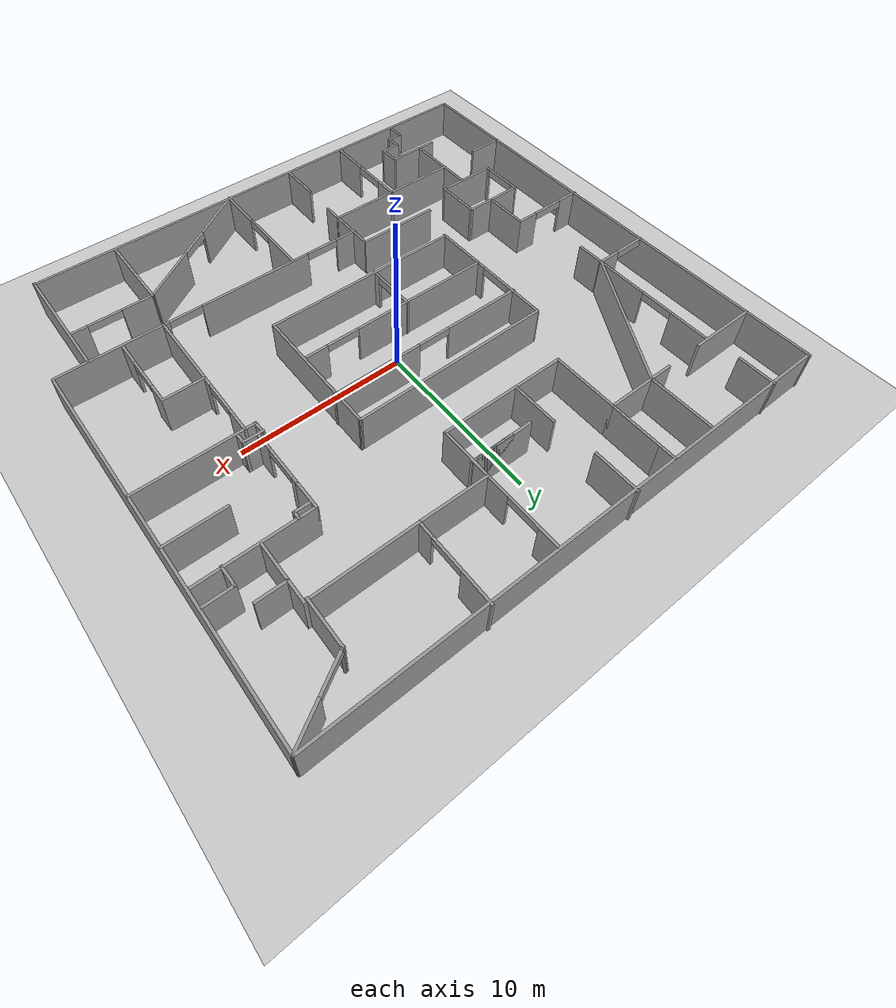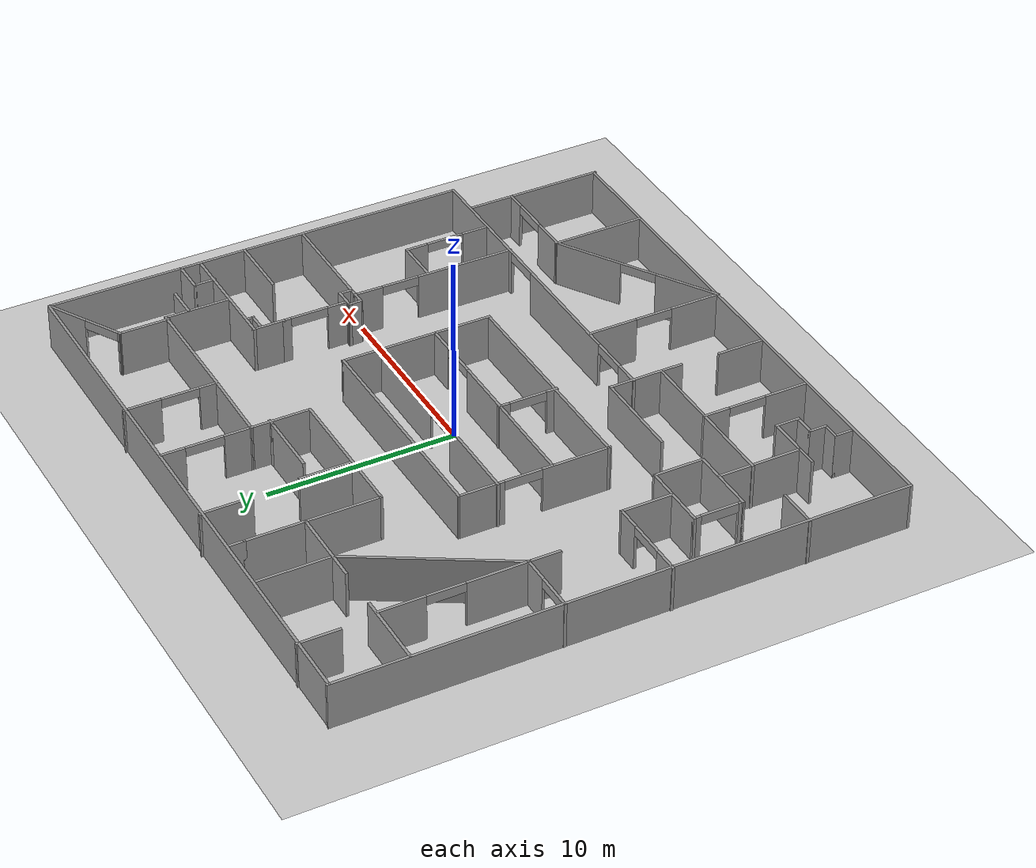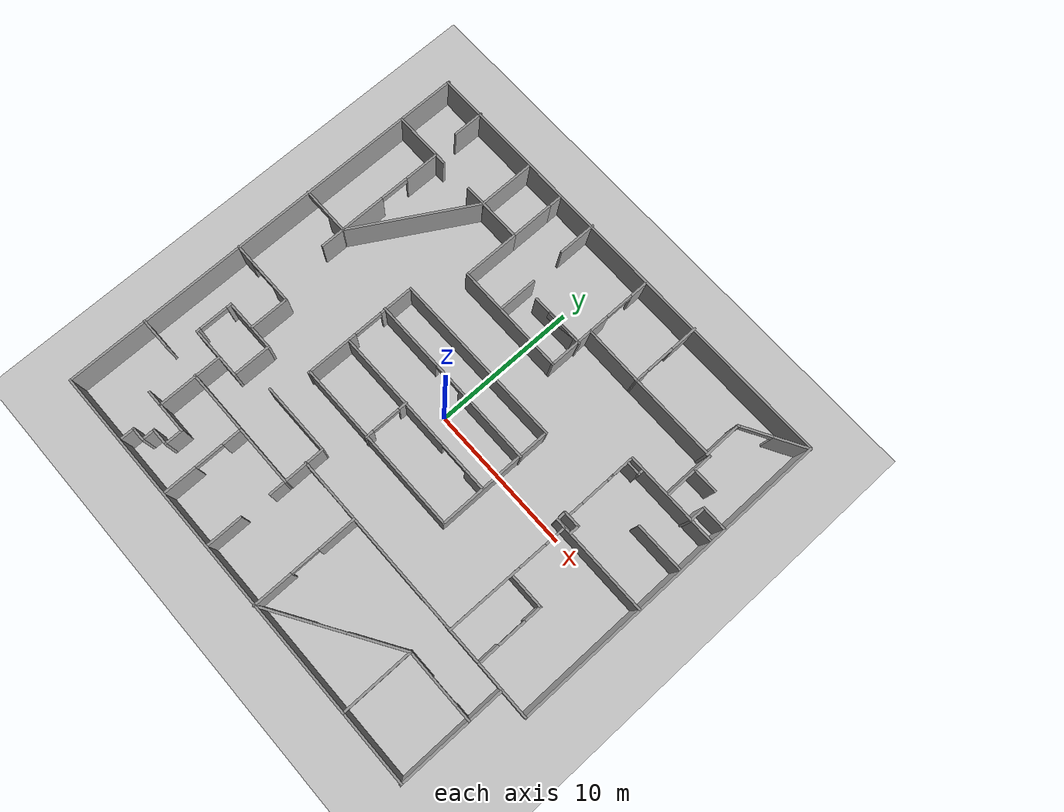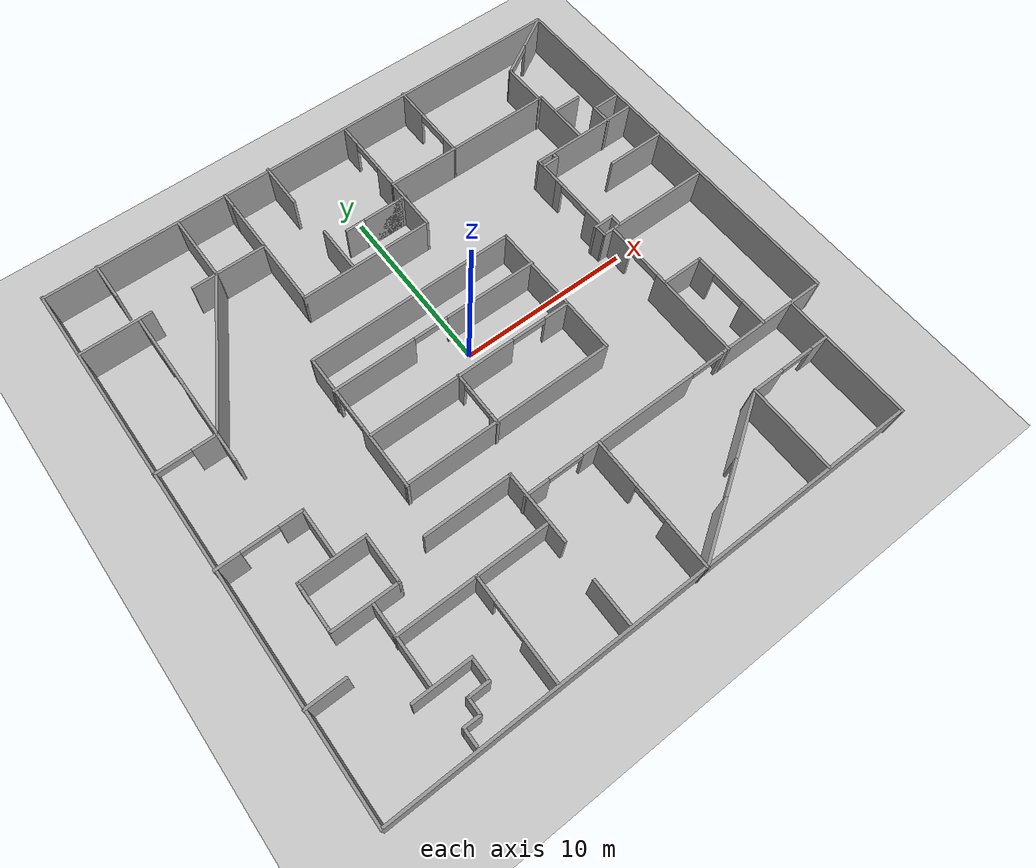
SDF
<sdf version="1.7">
 <world name="default">
  <light name="sun" type="directional">
   <pose>0 0 10 0 -0 0</pose>
   <diffuse>0.8 0.8 0.8 1</diffuse>
   <specular>0.2 0.2 0.2 1</specular>
   <attenuation>
    <range>1000</range>
    <constant>0.9</constant>
    <linear>0.01</linear>
    <quadratic>0.001</quadratic>
   </attenuation>
   <direction>-0.5 0.1 -0.9</direction>
   <spot><inner_angle>0</inner_angle><outer_angle>0</outer_angle><falloff>0</falloff></spot>
  </light>
  <model name="ground_plane">
   <static>1</static>
   <link name="link">
    <collision name="collision">
     <geometry><plane><normal>0 0 1</normal><size>100 100</size></plane></geometry>
     <surface><friction><ode><mu>100</mu><mu2>50</mu2></ode></friction></surface>
    </collision>
    <visual name="visual">
     <cast_shadows>0</cast_shadows>
     <geometry><plane><normal>0 0 1</normal><size>100 100</size></plane></geometry>
     <material>
      <script><uri>file://media/materials/scripts/gazebo.material</uri><name>Gazebo/Grey</name></script>
     </material>
    </visual>
   </link>
  </model>
  <gravity>0 0 -9.8</gravity>
  <magnetic_field>6e-06 2.3e-05 -4.2e-05</magnetic_field>
  <atmosphere type="adiabatic"/>
  <physics type="ode">
   <max_step_size>0.001</max_step_size>
   <real_time_factor>1</real_time_factor>
   <real_time_update_rate>1000</real_time_update_rate>
  </physics>
  <scene><ambient>0.4 0.4 0.4 1</ambient><background>0.7 0.7 0.7 1</background><shadows>1</shadows></scene>
  <audio><device>default</device></audio>
  <spherical_coordinates>
   <surface_model>EARTH_WGS84</surface_model>
   <latitude_deg>0</latitude_deg>
   <longitude_deg>0</longitude_deg>
   <elevation>0</elevation>
   <heading_deg>0</heading_deg>
  </spherical_coordinates>
  <model name="Untitled">
   <pose>-0.105598 -0.502872 0 0 -0 0</pose>
   <link name="Wall_0">
    <collision name="Wall_0_Collision">
     <geometry><box><size>32 0.15 2.5</size></box></geometry>
     <pose>0 0 1.25 0 -0 0</pose>
    </collision>
    <visual name="Wall_0_Visual">
     <pose>0 0 1.25 0 -0 0</pose>
     <geometry><box><size>32 0.15 2.5</size></box></geometry>
     <material>
      <script><uri>file://media/materials/scripts/gazebo.material</uri><name>Gazebo/Grey</name></script>
      <ambient>1 1 1 1</ambient>
     </material>
     <meta><layer>0</layer></meta>
    </visual>
    <pose>-0.015819 14.9519 0 0 -0 0</pose>
   </link>
   <link name="Wall_10">
    <pose>-6.94082 -0.072116 0 0 -0 1.5708</pose>
    <visual name="Wall_10_Visual_0">
     <pose>-2.22777 0 1.25 0 -0 0</pose>
     <geometry><box><size>3.69446 0.15 2.5</size></box></geometry>
     <material>
      <script><uri>file://media/materials/scripts/gazebo.material</uri><name>Gazebo/Grey</name></script>
      <ambient>1 1 1 1</ambient>
     </material>
     <meta><layer>0</layer></meta>
    </visual>
    <collision name="Wall_10_Collision_0">
     <geometry><box><size>3.69446 0.15 2.5</size></box></geometry>
     <pose>-2.22777 0 1.25 0 -0 0</pose>
    </collision>
    <visual name="Wall_10_Visual_1">
     <pose>2.84723 0 1.25 0 -0 0</pose>
     <geometry><box><size>2.45554 0.15 2.5</size></box></geometry>
     <material>
      <script><uri>file://media/materials/scripts/gazebo.material</uri><name>Gazebo/Grey</name></script>
      <ambient>1 1 1 1</ambient>
     </material>
     <meta><layer>0</layer></meta>
    </visual>
    <collision name="Wall_10_Collision_1">
     <geometry><box><size>2.45554 0.15 2.5</size></box></geometry>
     <pose>2.84723 0 1.25 0 -0 0</pose>
    </collision>
    <visual name="Wall_10_Visual_2">
     <pose>0.619458 0 2.25 0 -0 0</pose>
     <geometry><box><size>2 0.15 0.5</size></box></geometry>
     <material>
      <script><uri>file://media/materials/scripts/gazebo.material</uri><name>Gazebo/Grey</name></script>
      <ambient>1 1 1 1</ambient>
     </material>
     <meta><layer>0</layer></meta>
    </visual>
    <collision name="Wall_10_Collision_2">
     <geometry><box><size>2 0.15 0.5</size></box></geometry>
     <pose>0.619458 0 2.25 0 -0 0</pose>
    </collision>
   </link>
   <link name="Wall_100">
    <pose>12.1601 -5.34541 0 0 -0 -1.5708</pose>
    <visual name="Wall_100_Visual_0">
     <pose>-1.76137 0 1.25 0 -0 0</pose>
     <geometry><box><size>1.22725 0.15 2.5</size></box></geometry>
     <material>
      <script><uri>file://media/materials/scripts/gazebo.material</uri><name>Gazebo/Grey</name></script>
      <ambient>1 1 1 1</ambient>
     </material>
     <meta><layer>0</layer></meta>
    </visual>
    <collision name="Wall_100_Collision_0">
     <geometry><box><size>1.22725 0.15 2.5</size></box></geometry>
     <pose>-1.76137 0 1.25 0 -0 0</pose>
    </collision>
    <visual name="Wall_100_Visual_1">
     <pose>1.61363 0 1.25 0 -0 0</pose>
     <geometry><box><size>1.52275 0.15 2.5</size></box></geometry>
     <material>
      <script><uri>file://media/materials/scripts/gazebo.material</uri><name>Gazebo/Grey</name></script>
      <ambient>1 1 1 1</ambient>
     </material>
     <meta><layer>0</layer></meta>
    </visual>
    <collision name="Wall_100_Collision_1">
     <geometry><box><size>1.52275 0.15 2.5</size></box></geometry>
     <pose>1.61363 0 1.25 0 -0 0</pose>
    </collision>
    <visual name="Wall_100_Visual_2">
     <pose>-0.147748 0 2.25 0 -0 0</pose>
     <geometry><box><size>2 0.15 0.5</size></box></geometry>
     <material>
      <script><uri>file://media/materials/scripts/gazebo.material</uri><name>Gazebo/Grey</name></script>
      <ambient>1 1 1 1</ambient>
     </material>
     <meta><layer>0</layer></meta>
    </visual>
    <collision name="Wall_100_Collision_2">
     <geometry><box><size>2 0.15 0.5</size></box></geometry>
     <pose>-0.147748 0 2.25 0 -0 0</pose>
    </collision>
   </link>
   <link name="Wall_102">
    <collision name="Wall_102_Collision">
     <geometry><box><size>0.75 0.15 2.5</size></box></geometry>
     <pose>0 0 1.25 0 -0 0</pose>
    </collision>
    <visual name="Wall_102_Visual">
     <pose>0 0 1.25 0 -0 0</pose>
     <geometry><box><size>0.75 0.15 2.5</size></box></geometry>
     <material>
      <script><uri>file://media/materials/scripts/gazebo.material</uri><name>Gazebo/Grey</name></script>
      <ambient>1 1 1 1</ambient>
     </material>
     <meta><layer>0</layer></meta>
    </visual>
    <pose>9.52193 1.02364 0 0 -0 3.14159</pose>
   </link>
   <link name="Wall_103">
    <collision name="Wall_103_Collision">
     <geometry><box><size>0.773696 0.15 2.5</size></box></geometry>
     <pose>0 0 1.25 0 -0 0</pose>
    </collision>
    <visual name="Wall_103_Visual">
     <pose>0 0 1.25 0 -0 0</pose>
     <geometry><box><size>0.773696 0.15 2.5</size></box></geometry>
     <material>
      <script><uri>file://media/materials/scripts/gazebo.material</uri><name>Gazebo/Grey</name></script>
      <ambient>1 1 1 1</ambient>
     </material>
     <meta><layer>0</layer></meta>
    </visual>
    <pose>9.2103 1.33527 0 0 -0 1.6081</pose>
   </link>
   <link name="Wall_104">
    <collision name="Wall_104_Collision">
     <geometry><box><size>1.25 0.15 2.5</size></box></geometry>
     <pose>0 0 1.25 0 -0 0</pose>
    </collision>
    <visual name="Wall_104_Visual">
     <pose>0 0 1.25 0 -0 0</pose>
     <geometry><box><size>1.25 0.15 2.5</size></box></geometry>
     <material>
      <script><uri>file://media/materials/scripts/gazebo.material</uri><name>Gazebo/Grey</name></script>
      <ambient>1 1 1 1</ambient>
     </material>
     <meta><layer>0</layer></meta>
    </visual>
    <pose>9.72541 1.6469 0 0 -0 0</pose>
   </link>
   <link name="Wall_107">
    <collision name="Wall_107_Collision">
     <geometry><box><size>0.75 0.15 2.5</size></box></geometry>
     <pose>0 0 1.25 0 -0 0</pose>
    </collision>
    <visual name="Wall_107_Visual">
     <pose>0 0 1.25 0 -0 0</pose>
     <geometry><box><size>0.75 0.15 2.5</size></box></geometry>
     <material>
      <script><uri>file://media/materials/scripts/gazebo.material</uri><name>Gazebo/Grey</name></script>
      <ambient>1 1 1 1</ambient>
     </material>
     <meta><layer>0</layer></meta>
    </visual>
    <pose>10.2754 1.3469 0 0 -0 -1.5708</pose>
   </link>
   <link name="Wall_109">
    <pose>9.47135 3.47041 0 0 -0 1.5708</pose>
    <visual name="Wall_109_Visual_0">
     <pose>-1.23605 0 1.25 0 -0 0</pose>
     <geometry><box><size>1.0279 0.15 2.5</size></box></geometry>
     <material>
      <script><uri>file://media/materials/scripts/gazebo.material</uri><name>Gazebo/Grey</name></script>
      <ambient>1 1 1 1</ambient>
     </material>
     <meta><layer>0</layer></meta>
    </visual>
    <collision name="Wall_109_Collision_0">
     <geometry><box><size>1.0279 0.15 2.5</size></box></geometry>
     <pose>-1.23605 0 1.25 0 -0 0</pose>
    </collision>
    <visual name="Wall_109_Visual_1">
     <pose>1.51395 0 1.25 0 -0 0</pose>
     <geometry><box><size>0.472105 0.15 2.5</size></box></geometry>
     <material>
      <script><uri>file://media/materials/scripts/gazebo.material</uri><name>Gazebo/Grey</name></script>
      <ambient>1 1 1 1</ambient>
     </material>
     <meta><layer>0</layer></meta>
    </visual>
    <collision name="Wall_109_Collision_1">
     <geometry><box><size>0.472105 0.15 2.5</size></box></geometry>
     <pose>1.51395 0 1.25 0 -0 0</pose>
    </collision>
    <visual name="Wall_109_Visual_2">
     <pose>0.277895 0 2.25 0 -0 0</pose>
     <geometry><box><size>2 0.15 0.5</size></box></geometry>
     <material>
      <script><uri>file://media/materials/scripts/gazebo.material</uri><name>Gazebo/Grey</name></script>
      <ambient>1 1 1 1</ambient>
     </material>
     <meta><layer>0</layer></meta>
    </visual>
    <collision name="Wall_109_Collision_2">
     <geometry><box><size>2 0.15 0.5</size></box></geometry>
     <pose>0.277895 0 2.25 0 -0 0</pose>
    </collision>
   </link>
   <link name="Wall_110">
    <collision name="Wall_110_Collision">
     <geometry><box><size>1.75 0.15 2.5</size></box></geometry>
     <pose>0 0 1.25 0 -0 0</pose>
    </collision>
    <visual name="Wall_110_Visual">
     <pose>0 0 1.25 0 -0 0</pose>
     <geometry><box><size>1.75 0.15 2.5</size></box></geometry>
     <material>
      <script><uri>file://media/materials/scripts/gazebo.material</uri><name>Gazebo/Grey</name></script>
      <ambient>1 1 1 1</ambient>
     </material>
     <meta><layer>0</layer></meta>
    </visual>
    <pose>9.47135 5.94541 0 0 -0 1.5708</pose>
   </link>
   <link name="Wall_111">
    <collision name="Wall_111_Collision">
     <geometry><box><size>6.5 0.15 2.5</size></box></geometry>
     <pose>0 0 1.25 0 -0 0</pose>
    </collision>
    <visual name="Wall_111_Visual">
     <pose>0 0 1.25 0 -0 0</pose>
     <geometry><box><size>6.5 0.15 2.5</size></box></geometry>
     <material>
      <script><uri>file://media/materials/scripts/gazebo.material</uri><name>Gazebo/Grey</name></script>
      <ambient>1 1 1 1</ambient>
     </material>
     <meta><layer>0</layer></meta>
    </visual>
    <pose>12.6463 6.74541 0 0 -0 0</pose>
   </link>
   <link name="Wall_113">
    <collision name="Wall_113_Collision">
     <geometry><box><size>3.5 0.15 2.5</size></box></geometry>
     <pose>0 0 1.25 0 -0 0</pose>
    </collision>
    <visual name="Wall_113_Visual">
     <pose>0 0 1.25 0 -0 0</pose>
     <geometry><box><size>3.5 0.15 2.5</size></box></geometry>
     <material>
      <script><uri>file://media/materials/scripts/gazebo.material</uri><name>Gazebo/Grey</name></script>
      <ambient>1 1 1 1</ambient>
     </material>
     <meta><layer>0</layer></meta>
    </visual>
    <pose>14.2653 4.27721 0 0 -0 3.14159</pose>
   </link>
   <link name="Wall_115">
    <collision name="Wall_115_Collision">
     <geometry><box><size>0.5 0.15 2.5</size></box></geometry>
     <pose>0 0 1.25 0 -0 0</pose>
    </collision>
    <visual name="Wall_115_Visual">
     <pose>0 0 1.25 0 -0 0</pose>
     <geometry><box><size>0.5 0.15 2.5</size></box></geometry>
     <material>
      <script><uri>file://media/materials/scripts/gazebo.material</uri><name>Gazebo/Grey</name></script>
      <ambient>1 1 1 1</ambient>
     </material>
     <meta><layer>0</layer></meta>
    </visual>
    <pose>10.4071 6.54333 0 0 -0 -1.5708</pose>
   </link>
   <link name="Wall_116">
    <collision name="Wall_116_Collision">
     <geometry><box><size>1 0.15 2.5</size></box></geometry>
     <pose>0 0 1.25 0 -0 0</pose>
    </collision>
    <visual name="Wall_116_Visual">
     <pose>0 0 1.25 0 -0 0</pose>
     <geometry><box><size>1 0.15 2.5</size></box></geometry>
     <material>
      <script><uri>file://media/materials/scripts/gazebo.material</uri><name>Gazebo/Grey</name></script>
      <ambient>1 1 1 1</ambient>
     </material>
     <meta><layer>0</layer></meta>
    </visual>
    <pose>9.98211 6.36833 0 0 -0 3.14159</pose>
   </link>
   <link name="Wall_118">
    <collision name="Wall_118_Collision">
     <geometry><box><size>3.5 0.15 2.5</size></box></geometry>
     <pose>0 0 1.25 0 -0 0</pose>
    </collision>
    <visual name="Wall_118_Visual">
     <pose>0 0 1.25 0 -0 0</pose>
     <geometry><box><size>3.5 0.15 2.5</size></box></geometry>
     <material>
      <script><uri>file://media/materials/scripts/gazebo.material</uri><name>Gazebo/Grey</name></script>
      <ambient>1 1 1 1</ambient>
     </material>
     <meta><layer>0</layer></meta>
    </visual>
    <pose>12.3892 8.52156 0 0 -0 1.5708</pose>
   </link>
   <link name="Wall_119">
    <collision name="Wall_119_Collision">
     <geometry><box><size>6.25 0.15 2.5</size></box></geometry>
     <pose>0 0 1.25 0 -0 0</pose>
    </collision>
    <visual name="Wall_119_Visual">
     <pose>0 0 1.25 0 -0 0</pose>
     <geometry><box><size>6.25 0.15 2.5</size></box></geometry>
     <material>
      <script><uri>file://media/materials/scripts/gazebo.material</uri><name>Gazebo/Grey</name></script>
      <ambient>1 1 1 1</ambient>
     </material>
     <meta><layer>0</layer></meta>
    </visual>
    <pose>9.33915 10.1966 0 0 -0 3.14159</pose>
   </link>
   <link name="Wall_12">
    <collision name="Wall_12_Collision">
     <geometry><box><size>12.15 0.15 2.5</size></box></geometry>
     <pose>0 0 1.25 0 -0 0</pose>
    </collision>
    <visual name="Wall_12_Visual">
     <pose>0 0 1.25 0 -0 0</pose>
     <geometry><box><size>12.15 0.15 2.5</size></box></geometry>
     <material>
      <script><uri>file://media/materials/scripts/gazebo.material</uri><name>Gazebo/Grey</name></script>
      <ambient>1 1 1 1</ambient>
     </material>
     <meta><layer>0</layer></meta>
    </visual>
    <pose>-0.940819 -4.00136 0 0 -0 0</pose>
   </link>
   <link name="Wall_121">
    <pose>6.28915 12.6216 0 0 -0 1.5708</pose>
    <visual name="Wall_121_Visual_0">
     <pose>-1.99093 0 1.25 0 -0 0</pose>
     <geometry><box><size>1.01815 0.15 2.5</size></box></geometry>
     <material>
      <script><uri>file://media/materials/scripts/gazebo.material</uri><name>Gazebo/Grey</name></script>
      <ambient>1 1 1 1</ambient>
     </material>
     <meta><layer>0</layer></meta>
    </visual>
    <collision name="Wall_121_Collision_0">
     <geometry><box><size>1.01815 0.15 2.5</size></box></geometry>
     <pose>-1.99093 0 1.25 0 -0 0</pose>
    </collision>
    <visual name="Wall_121_Visual_1">
     <pose>1.50907 0 1.25 0 -0 0</pose>
     <geometry><box><size>1.98185 0.15 2.5</size></box></geometry>
     <material>
      <script><uri>file://media/materials/scripts/gazebo.material</uri><name>Gazebo/Grey</name></script>
      <ambient>1 1 1 1</ambient>
     </material>
     <meta><layer>0</layer></meta>
    </visual>
    <collision name="Wall_121_Collision_1">
     <geometry><box><size>1.98185 0.15 2.5</size></box></geometry>
     <pose>1.50907 0 1.25 0 -0 0</pose>
    </collision>
    <visual name="Wall_121_Visual_2">
     <pose>-0.481853 0 2.25 0 -0 0</pose>
     <geometry><box><size>2 0.15 0.5</size></box></geometry>
     <material>
      <script><uri>file://media/materials/scripts/gazebo.material</uri><name>Gazebo/Grey</name></script>
      <ambient>1 1 1 1</ambient>
     </material>
     <meta><layer>0</layer></meta>
    </visual>
    <collision name="Wall_121_Collision_2">
     <geometry><box><size>2 0.15 0.5</size></box></geometry>
     <pose>-0.481853 0 2.25 0 -0 0</pose>
    </collision>
   </link>
   <link name="Wall_123">
    <pose>14.0857 13.8282 0 0 -0 -2.61799</pose>
    <visual name="Wall_123_Visual_0">
     <pose>-1.09346 0 1.25 0 -0 0</pose>
     <geometry><box><size>2.31309 0.15 2.5</size></box></geometry>
     <material>
      <script><uri>file://media/materials/scripts/gazebo.material</uri><name>Gazebo/Grey</name></script>
      <ambient>1 1 1 1</ambient>
     </material>
     <meta><layer>0</layer></meta>
    </visual>
    <collision name="Wall_123_Collision_0">
     <geometry><box><size>2.31309 0.15 2.5</size></box></geometry>
     <pose>-1.09346 0 1.25 0 -0 0</pose>
    </collision>
    <visual name="Wall_123_Visual_1">
     <pose>2.15654 0 1.25 0 -0 0</pose>
     <geometry><box><size>0.186911 0.15 2.5</size></box></geometry>
     <material>
      <script><uri>file://media/materials/scripts/gazebo.material</uri><name>Gazebo/Grey</name></script>
      <ambient>1 1 1 1</ambient>
     </material>
     <meta><layer>0</layer></meta>
    </visual>
    <collision name="Wall_123_Collision_1">
     <geometry><box><size>0.186911 0.15 2.5</size></box></geometry>
     <pose>2.15654 0 1.25 0 -0 0</pose>
    </collision>
    <visual name="Wall_123_Visual_2">
     <pose>1.06309 0 2.25 0 -0 0</pose>
     <geometry><box><size>2 0.15 0.5</size></box></geometry>
     <material>
      <script><uri>file://media/materials/scripts/gazebo.material</uri><name>Gazebo/Grey</name></script>
      <ambient>1 1 1 1</ambient>
     </material>
     <meta><layer>0</layer></meta>
    </visual>
    <collision name="Wall_123_Collision_2">
     <geometry><box><size>2 0.15 0.5</size></box></geometry>
     <pose>1.06309 0 2.25 0 -0 0</pose>
    </collision>
   </link>
   <link name="Wall_125">
    <collision name="Wall_125_Collision">
     <geometry><box><size>2.75 0.15 2.5</size></box></geometry>
     <pose>0 0 1.25 0 -0 0</pose>
    </collision>
    <visual name="Wall_125_Visual">
     <pose>0 0 1.25 0 -0 0</pose>
     <geometry><box><size>2.75 0.15 2.5</size></box></geometry>
     <material>
      <script><uri>file://media/materials/scripts/gazebo.material</uri><name>Gazebo/Grey</name></script>
      <ambient>1 1 1 1</ambient>
     </material>
     <meta><layer>0</layer></meta>
    </visual>
    <pose>12.2021 11.4407 0 0 -0 -1.5708</pose>
   </link>
   <link name="Wall_127">
    <collision name="Wall_127_Collision">
     <geometry><box><size>1.75 0.15 2.5</size></box></geometry>
     <pose>0 0 1.25 0 -0 0</pose>
    </collision>
    <visual name="Wall_127_Visual">
     <pose>0 0 1.25 0 -0 0</pose>
     <geometry><box><size>1.75 0.15 2.5</size></box></geometry>
     <material>
      <script><uri>file://media/materials/scripts/gazebo.material</uri><name>Gazebo/Grey</name></script>
      <ambient>1 1 1 1</ambient>
     </material>
     <meta><layer>0</layer></meta>
    </visual>
    <pose>13.2177 8.96513 0 0 -0 0</pose>
   </link>
   <link name="Wall_129">
    <collision name="Wall_129_Collision">
     <geometry><box><size>1.25 0.15 2.5</size></box></geometry>
     <pose>0 0 1.25 0 -0 0</pose>
    </collision>
    <visual name="Wall_129_Visual">
     <pose>0 0 1.25 0 -0 0</pose>
     <geometry><box><size>1.25 0.15 2.5</size></box></geometry>
     <material>
      <script><uri>file://media/materials/scripts/gazebo.material</uri><name>Gazebo/Grey</name></script>
      <ambient>1 1 1 1</ambient>
     </material>
     <meta><layer>0</layer></meta>
    </visual>
    <pose>14.3025 7.25087 0 0 -0 1.5708</pose>
   </link>
   <link name="Wall_130">
    <collision name="Wall_130_Collision">
     <geometry><box><size>1.75 0.15 2.5</size></box></geometry>
     <pose>0 0 1.25 0 -0 0</pose>
    </collision>
    <visual name="Wall_130_Visual">
     <pose>0 0 1.25 0 -0 0</pose>
     <geometry><box><size>1.75 0.15 2.5</size></box></geometry>
     <material>
      <script><uri>file://media/materials/scripts/gazebo.material</uri><name>Gazebo/Grey</name></script>
      <ambient>1 1 1 1</ambient>
     </material>
     <meta><layer>0</layer></meta>
    </visual>
    <pose>15.1025 7.80088 0 0 -0 0</pose>
   </link>
   <link name="Wall_132">
    <collision name="Wall_132_Collision">
     <geometry><box><size>3 0.15 2.5</size></box></geometry>
     <pose>0 0 1.25 0 -0 0</pose>
    </collision>
    <visual name="Wall_132_Visual">
     <pose>0 0 1.25 0 -0 0</pose>
     <geometry><box><size>3 0.15 2.5</size></box></geometry>
     <material>
      <script><uri>file://media/materials/scripts/gazebo.material</uri><name>Gazebo/Grey</name></script>
      <ambient>1 1 1 1</ambient>
     </material>
     <meta><layer>0</layer></meta>
    </visual>
    <pose>-6.7689 10.9946 0 0 -0 0</pose>
   </link>
   <link name="Wall_133">
    <collision name="Wall_133_Collision">
     <geometry><box><size>4 0.15 2.5</size></box></geometry>
     <pose>0 0 1.25 0 -0 0</pose>
    </collision>
    <visual name="Wall_133_Visual">
     <pose>0 0 1.25 0 -0 0</pose>
     <geometry><box><size>4 0.15 2.5</size></box></geometry>
     <material>
      <script><uri>file://media/materials/scripts/gazebo.material</uri><name>Gazebo/Grey</name></script>
      <ambient>1 1 1 1</ambient>
     </material>
     <meta><layer>0</layer></meta>
    </visual>
    <pose>-5.34389 9.06962 0 0 -0 -1.5708</pose>
   </link>
   <link name="Wall_134">
    <collision name="Wall_134_Collision">
     <geometry><box><size>7.75 0.15 2.5</size></box></geometry>
     <pose>0 0 1.25 0 -0 0</pose>
    </collision>
    <visual name="Wall_134_Visual">
     <pose>0 0 1.25 0 -0 0</pose>
     <geometry><box><size>7.75 0.15 2.5</size></box></geometry>
     <material>
      <script><uri>file://media/materials/scripts/gazebo.material</uri><name>Gazebo/Grey</name></script>
      <ambient>1 1 1 1</ambient>
     </material>
     <meta><layer>0</layer></meta>
    </visual>
    <pose>-1.5439 7.14462 0 0 -0 0</pose>
   </link>
   <link name="Wall_135">
    <collision name="Wall_135_Collision">
     <geometry><box><size>3.25 0.15 2.5</size></box></geometry>
     <pose>0 0 1.25 0 -0 0</pose>
    </collision>
    <visual name="Wall_135_Visual">
     <pose>0 0 1.25 0 -0 0</pose>
     <geometry><box><size>3.25 0.15 2.5</size></box></geometry>
     <material>
      <script><uri>file://media/materials/scripts/gazebo.material</uri><name>Gazebo/Grey</name></script>
      <ambient>1 1 1 1</ambient>
     </material>
     <meta><layer>0</layer></meta>
    </visual>
    <pose>2.2561 8.69462 0 0 -0 1.5708</pose>
   </link>
   <link name="Wall_136">
    <collision name="Wall_136_Collision">
     <geometry><box><size>4.18334 0.15 2.5</size></box></geometry>
     <pose>0 0 1.25 0 -0 0</pose>
    </collision>
    <visual name="Wall_136_Visual">
     <pose>0 0 1.25 0 -0 0</pose>
     <geometry><box><size>4.18334 0.15 2.5</size></box></geometry>
     <material>
      <script><uri>file://media/materials/scripts/gazebo.material</uri><name>Gazebo/Grey</name></script>
      <ambient>1 1 1 1</ambient>
     </material>
     <meta><layer>0</layer></meta>
    </visual>
    <pose>4.27263 10.2206 0 0 -0 -0.011916</pose>
   </link>
   <link name="Wall_138">
    <collision name="Wall_138_Collision">
     <geometry><box><size>3.25 0.15 2.5</size></box></geometry>
     <pose>0 0 1.25 0 -0 0</pose>
    </collision>
    <visual name="Wall_138_Visual">
     <pose>0 0 1.25 0 -0 0</pose>
     <geometry><box><size>3.25 0.15 2.5</size></box></geometry>
     <material>
      <script><uri>file://media/materials/scripts/gazebo.material</uri><name>Gazebo/Grey</name></script>
      <ambient>1 1 1 1</ambient>
     </material>
     <meta><layer>0</layer></meta>
    </visual>
    <pose>-5.34389 12.5446 0 0 -0 1.5708</pose>
   </link>
   <link name="Wall_139">
    <collision name="Wall_139_Collision">
     <geometry><box><size>1 0.15 2.5</size></box></geometry>
     <pose>0 0 1.25 0 -0 0</pose>
    </collision>
    <visual name="Wall_139_Visual">
     <pose>0 0 1.25 0 -0 0</pose>
     <geometry><box><size>1 0.15 2.5</size></box></geometry>
     <material>
      <script><uri>file://media/materials/scripts/gazebo.material</uri><name>Gazebo/Grey</name></script>
      <ambient>1 1 1 1</ambient>
     </material>
     <meta><layer>0</layer></meta>
    </visual>
    <pose>-5.34389 14.5196 0 0 -0 1.5708</pose>
   </link>
   <link name="Wall_14">
    <collision name="Wall_14_Collision">
     <geometry><box><size>8.15 0.15 2.5</size></box></geometry>
     <pose>0 0 1.25 0 -0 0</pose>
    </collision>
    <visual name="Wall_14_Visual">
     <pose>0 0 1.25 0 -0 0</pose>
     <geometry><box><size>8.15 0.15 2.5</size></box></geometry>
     <material>
      <script><uri>file://media/materials/scripts/gazebo.material</uri><name>Gazebo/Grey</name></script>
      <ambient>1 1 1 1</ambient>
     </material>
     <meta><layer>0</layer></meta>
    </visual>
    <pose>5.05918 -0.001359 0 0 -0 1.5708</pose>
   </link>
   <link name="Wall_141">
    <collision name="Wall_141_Collision">
     <geometry><box><size>2.75 0.15 2.5</size></box></geometry>
     <pose>0 0 1.25 0 -0 0</pose>
    </collision>
    <visual name="Wall_141_Visual">
     <pose>0 0 1.25 0 -0 0</pose>
     <geometry><box><size>2.75 0.15 2.5</size></box></geometry>
     <material>
      <script><uri>file://media/materials/scripts/gazebo.material</uri><name>Gazebo/Grey</name></script>
      <ambient>1 1 1 1</ambient>
     </material>
     <meta><layer>0</layer></meta>
    </visual>
    <pose>-2.3552 8.55347 0 0 -0 1.5708</pose>
   </link>
   <link name="Wall_143">
    <collision name="Wall_143_Collision">
     <geometry><box><size>2.75 0.15 2.5</size></box></geometry>
     <pose>0 0 1.25 0 -0 0</pose>
    </collision>
    <visual name="Wall_143_Visual">
     <pose>0 0 1.25 0 -0 0</pose>
     <geometry><box><size>2.75 0.15 2.5</size></box></geometry>
     <material>
      <script><uri>file://media/materials/scripts/gazebo.material</uri><name>Gazebo/Grey</name></script>
      <ambient>1 1 1 1</ambient>
     </material>
     <meta><layer>0</layer></meta>
    </visual>
    <pose>-2.61835 13.7628 0 0 -0 -1.5708</pose>
   </link>
   <link name="Wall_145">
    <pose>0.299408 9.22055 0 0 -0 0</pose>
    <visual name="Wall_145_Visual_0">
     <pose>0 0 1.25 0 -0 0</pose>
     <geometry><box><size>3.5 0.15 2.5</size></box></geometry>
     <material>
      <script><uri>file://media/materials/scripts/gazebo.material</uri><name>Gazebo/Grey</name></script>
      <ambient>1 1 1 1</ambient>
     </material>
     <meta><layer>0</layer></meta>
    </visual>
    <collision name="Wall_145_Collision_0">
     <geometry><box><size>3.5 0.15 2.5</size></box></geometry>
     <pose>0 0 1.25 0 -0 0</pose>
    </collision>
    <visual name="Wall_145_Visual_1">
     <pose>0.58502 0 1.25 0 -0 0</pose>
     <geometry><box><size>2.32996 0.15 2.5</size></box></geometry>
     <material>
      <script><uri>file://media/materials/scripts/gazebo.material</uri><name>Gazebo/Grey</name></script>
      <ambient>1 1 1 1</ambient>
     </material>
     <meta><layer>0</layer></meta>
    </visual>
    <collision name="Wall_145_Collision_1">
     <geometry><box><size>2.32996 0.15 2.5</size></box></geometry>
     <pose>0.58502 0 1.25 0 -0 0</pose>
    </collision>
   </link>
   <link name="Wall_146">
    <collision name="Wall_146_Collision">
     <geometry><box><size>0.5 0.15 2.5</size></box></geometry>
     <pose>0 0 1.25 0 -0 0</pose>
    </collision>
    <visual name="Wall_146_Visual">
     <pose>0 0 1.25 0 -0 0</pose>
     <geometry><box><size>0.5 0.15 2.5</size></box></geometry>
     <material>
      <script><uri>file://media/materials/scripts/gazebo.material</uri><name>Gazebo/Grey</name></script>
      <ambient>1 1 1 1</ambient>
     </material>
     <meta><layer>0</layer></meta>
    </visual>
    <pose>2.14941 9.22055 0 0 -0 0</pose>
   </link>
   <link name="Wall_148">
    <pose>2.2561 12.5446 0 0 -0 1.5708</pose>
    <visual name="Wall_148_Visual_0">
     <pose>-1.63102 0 1.25 0 -0 0</pose>
     <geometry><box><size>1.48795 0.15 2.5</size></box></geometry>
     <material>
      <script><uri>file://media/materials/scripts/gazebo.material</uri><name>Gazebo/Grey</name></script>
      <ambient>1 1 1 1</ambient>
     </material>
     <meta><layer>0</layer></meta>
    </visual>
    <collision name="Wall_148_Collision_0">
     <geometry><box><size>1.48795 0.15 2.5</size></box></geometry>
     <pose>-1.63102 0 1.25 0 -0 0</pose>
    </collision>
    <visual name="Wall_148_Visual_1">
     <pose>1.74398 0 1.25 0 -0 0</pose>
     <geometry><box><size>1.26205 0.15 2.5</size></box></geometry>
     <material>
      <script><uri>file://media/materials/scripts/gazebo.material</uri><name>Gazebo/Grey</name></script>
      <ambient>1 1 1 1</ambient>
     </material>
     <meta><layer>0</layer></meta>
    </visual>
    <collision name="Wall_148_Collision_1">
     <geometry><box><size>1.26205 0.15 2.5</size></box></geometry>
     <pose>1.74398 0 1.25 0 -0 0</pose>
    </collision>
    <visual name="Wall_148_Visual_2">
     <pose>0.112949 0 2.25 0 -0 0</pose>
     <geometry><box><size>2 0.15 0.5</size></box></geometry>
     <material>
      <script><uri>file://media/materials/scripts/gazebo.material</uri><name>Gazebo/Grey</name></script>
      <ambient>1 1 1 1</ambient>
     </material>
     <meta><layer>0</layer></meta>
    </visual>
    <collision name="Wall_148_Collision_2">
     <geometry><box><size>2 0.15 0.5</size></box></geometry>
     <pose>0.112949 0 2.25 0 -0 0</pose>
    </collision>
   </link>
   <link name="Wall_16">
    <collision name="Wall_16_Collision">
     <geometry><box><size>12.1502 0.15 2.5</size></box></geometry>
     <pose>0 0 1.25 0 -0 0</pose>
    </collision>
    <visual name="Wall_16_Visual">
     <pose>0 0 1.25 0 -0 0</pose>
     <geometry><box><size>12.1502 0.15 2.5</size></box></geometry>
     <material>
      <script><uri>file://media/materials/scripts/gazebo.material</uri><name>Gazebo/Grey</name></script>
      <ambient>1 1 1 1</ambient>
     </material>
     <meta><layer>0</layer></meta>
    </visual>
    <pose>-0.940819 3.96326 0 0 -0 0.005896</pose>
   </link>
   <link name="Wall_18">
    <pose>-0.932893 -1.01205 0 0 -0 0</pose>
    <visual name="Wall_18_Visual_0">
     <pose>-1.73618 0 1.25 0 -0 0</pose>
     <geometry><box><size>8.52764 0.15 2.5</size></box></geometry>
     <material>
      <script><uri>file://media/materials/scripts/gazebo.material</uri><name>Gazebo/Grey</name></script>
      <ambient>1 1 1 1</ambient>
     </material>
     <meta><layer>0</layer></meta>
    </visual>
    <collision name="Wall_18_Collision_0">
     <geometry><box><size>8.52764 0.15 2.5</size></box></geometry>
     <pose>-1.73618 0 1.25 0 -0 0</pose>
    </collision>
    <visual name="Wall_18_Visual_1">
     <pose>5.26382 0 1.25 0 -0 0</pose>
     <geometry><box><size>1.47236 0.15 2.5</size></box></geometry>
     <material>
      <script><uri>file://media/materials/scripts/gazebo.material</uri><name>Gazebo/Grey</name></script>
      <ambient>1 1 1 1</ambient>
     </material>
     <meta><layer>0</layer></meta>
    </visual>
    <collision name="Wall_18_Collision_1">
     <geometry><box><size>1.47236 0.15 2.5</size></box></geometry>
     <pose>5.26382 0 1.25 0 -0 0</pose>
    </collision>
    <visual name="Wall_18_Visual_2">
     <pose>3.52764 0 2.25 0 -0 0</pose>
     <geometry><box><size>2 0.15 0.5</size></box></geometry>
     <material>
      <script><uri>file://media/materials/scripts/gazebo.material</uri><name>Gazebo/Grey</name></script>
      <ambient>1 1 1 1</ambient>
     </material>
     <meta><layer>0</layer></meta>
    </visual>
    <collision name="Wall_18_Collision_2">
     <geometry><box><size>2 0.15 0.5</size></box></geometry>
     <pose>3.52764 0 2.25 0 -0 0</pose>
    </collision>
   </link>
   <link name="Wall_20">
    <pose>-1.71937 -2.51877 0 0 -0 -1.5708</pose>
    <visual name="Wall_20_Visual_0">
     <pose>-1.30824 0 1.25 0 -0 0</pose>
     <geometry><box><size>0.633515 0.15 2.5</size></box></geometry>
     <material>
      <script><uri>file://media/materials/scripts/gazebo.material</uri><name>Gazebo/Grey</name></script>
      <ambient>1 1 1 1</ambient>
     </material>
     <meta><layer>0</layer></meta>
    </visual>
    <collision name="Wall_20_Collision_0">
     <geometry><box><size>0.633515 0.15 2.5</size></box></geometry>
     <pose>-1.30824 0 1.25 0 -0 0</pose>
    </collision>
    <visual name="Wall_20_Visual_1">
     <pose>1.31676 0 1.25 0 -0 0</pose>
     <geometry><box><size>0.616485 0.15 2.5</size></box></geometry>
     <material>
      <script><uri>file://media/materials/scripts/gazebo.material</uri><name>Gazebo/Grey</name></script>
      <ambient>1 1 1 1</ambient>
     </material>
     <meta><layer>0</layer></meta>
    </visual>
    <collision name="Wall_20_Collision_1">
     <geometry><box><size>0.616485 0.15 2.5</size></box></geometry>
     <pose>1.31676 0 1.25 0 -0 0</pose>
    </collision>
    <visual name="Wall_20_Visual_2">
     <pose>0.008515 0 2.25 0 -0 0</pose>
     <geometry><box><size>2 0.15 0.5</size></box></geometry>
     <material>
      <script><uri>file://media/materials/scripts/gazebo.material</uri><name>Gazebo/Grey</name></script>
      <ambient>1 1 1 1</ambient>
     </material>
     <meta><layer>0</layer></meta>
    </visual>
    <collision name="Wall_20_Collision_2">
     <geometry><box><size>2 0.15 0.5</size></box></geometry>
     <pose>0.008515 0 2.25 0 -0 0</pose>
    </collision>
   </link>
   <link name="Wall_22">
    <pose>-0.939938 1.92283 0 0 -0 0</pose>
    <visual name="Wall_22_Visual_0">
     <pose>-3.72488 0 1.25 0 -0 0</pose>
     <geometry><box><size>4.80023 0.15 2.5</size></box></geometry>
     <material>
      <script><uri>file://media/materials/scripts/gazebo.material</uri><name>Gazebo/Grey</name></script>
      <ambient>1 1 1 1</ambient>
     </material>
     <meta><layer>0</layer></meta>
    </visual>
    <collision name="Wall_22_Collision_0">
     <geometry><box><size>4.80023 0.15 2.5</size></box></geometry>
     <pose>-3.72488 0 1.25 0 -0 0</pose>
    </collision>
    <visual name="Wall_22_Visual_1">
     <pose>3.40012 0 1.25 0 -0 0</pose>
     <geometry><box><size>5.44977 0.15 2.5</size></box></geometry>
     <material>
      <script><uri>file://media/materials/scripts/gazebo.material</uri><name>Gazebo/Grey</name></script>
      <ambient>1 1 1 1</ambient>
     </material>
     <meta><layer>0</layer></meta>
    </visual>
    <collision name="Wall_22_Collision_1">
     <geometry><box><size>5.44977 0.15 2.5</size></box></geometry>
     <pose>3.40012 0 1.25 0 -0 0</pose>
    </collision>
    <visual name="Wall_22_Visual_2">
     <pose>-0.324766 0 2.25 0 -0 0</pose>
     <geometry><box><size>2 0.15 0.5</size></box></geometry>
     <material>
      <script><uri>file://media/materials/scripts/gazebo.material</uri><name>Gazebo/Grey</name></script>
      <ambient>1 1 1 1</ambient>
     </material>
     <meta><layer>0</layer></meta>
    </visual>
    <collision name="Wall_22_Collision_2">
     <geometry><box><size>2 0.15 0.5</size></box></geometry>
     <pose>-0.324766 0 2.25 0 -0 0</pose>
    </collision>
   </link>
   <link name="Wall_24">
    <collision name="Wall_24_Collision">
     <geometry><box><size>4.15 0.15 2.5</size></box></geometry>
     <pose>0 0 1.25 0 -0 0</pose>
    </collision>
    <visual name="Wall_24_Visual">
     <pose>0 0 1.25 0 -0 0</pose>
     <geometry><box><size>4.15 0.15 2.5</size></box></geometry>
     <material>
      <script><uri>file://media/materials/scripts/gazebo.material</uri><name>Gazebo/Grey</name></script>
      <ambient>1 1 1 1</ambient>
     </material>
     <meta><layer>0</layer></meta>
    </visual>
    <pose>-13.9408 10.9986 0 0 -0 0</pose>
   </link>
   <link name="Wall_26">
    <collision name="Wall_26_Collision">
     <geometry><box><size>1.5 0.15 2.5</size></box></geometry>
     <pose>0 0 1.25 0 -0 0</pose>
    </collision>
    <visual name="Wall_26_Visual">
     <pose>0 0 1.25 0 -0 0</pose>
     <geometry><box><size>1.5 0.15 2.5</size></box></geometry>
     <material>
      <script><uri>file://media/materials/scripts/gazebo.material</uri><name>Gazebo/Grey</name></script>
      <ambient>1 1 1 1</ambient>
     </material>
     <meta><layer>0</layer></meta>
    </visual>
    <pose>-8.8689 10.9946 0 0 -0 0</pose>
   </link>
   <link name="Wall_27">
    <collision name="Wall_27_Collision">
     <geometry><box><size>4 0.15 2.5</size></box></geometry>
     <pose>0 0 1.25 0 -0 0</pose>
    </collision>
    <visual name="Wall_27_Visual">
     <pose>0 0 1.25 0 -0 0</pose>
     <geometry><box><size>4 0.15 2.5</size></box></geometry>
     <material>
      <script><uri>file://media/materials/scripts/gazebo.material</uri><name>Gazebo/Grey</name></script>
      <ambient>1 1 1 1</ambient>
     </material>
     <meta><layer>0</layer></meta>
    </visual>
    <pose>-8.19389 12.9196 0 0 -0 1.5708</pose>
   </link>
   <link name="Wall_29">
    <collision name="Wall_29_Collision">
     <geometry><box><size>9 0.15 2.5</size></box></geometry>
     <pose>0 0 1.25 0 -0 0</pose>
    </collision>
    <visual name="Wall_29_Visual">
     <pose>0 0 1.25 0 -0 0</pose>
     <geometry><box><size>9 0.15 2.5</size></box></geometry>
     <material>
      <script><uri>file://media/materials/scripts/gazebo.material</uri><name>Gazebo/Grey</name></script>
      <ambient>1 1 1 1</ambient>
     </material>
     <meta><layer>0</layer></meta>
    </visual>
    <pose>-10.4064 7.16245 0 0 -0 -2.0944</pose>
   </link>
   <link name="Wall_33">
    <pose>-14.2939 3.33029 0 0 -0 3.14159</pose>
    <visual name="Wall_33_Visual_0">
     <pose>-1.02372 0 1.25 0 -0 0</pose>
     <geometry><box><size>1.45256 0.15 2.5</size></box></geometry>
     <material>
      <script><uri>file://media/materials/scripts/gazebo.material</uri><name>Gazebo/Grey</name></script>
      <ambient>1 1 1 1</ambient>
     </material>
     <meta><layer>0</layer></meta>
    </visual>
    <collision name="Wall_33_Collision_0">
     <geometry><box><size>1.45256 0.15 2.5</size></box></geometry>
     <pose>-1.02372 0 1.25 0 -0 0</pose>
    </collision>
    <visual name="Wall_33_Visual_1">
     <pose>1.72628 0 1.25 0 -0 0</pose>
     <geometry><box><size>0.047445 0.15 2.5</size></box></geometry>
     <material>
      <script><uri>file://media/materials/scripts/gazebo.material</uri><name>Gazebo/Grey</name></script>
      <ambient>1 1 1 1</ambient>
     </material>
     <meta><layer>0</layer></meta>
    </visual>
    <collision name="Wall_33_Collision_1">
     <geometry><box><size>0.047445 0.15 2.5</size></box></geometry>
     <pose>1.72628 0 1.25 0 -0 0</pose>
    </collision>
    <visual name="Wall_33_Visual_2">
     <pose>0.702555 0 2.25 0 -0 0</pose>
     <geometry><box><size>2 0.15 0.5</size></box></geometry>
     <material>
      <script><uri>file://media/materials/scripts/gazebo.material</uri><name>Gazebo/Grey</name></script>
      <ambient>1 1 1 1</ambient>
     </material>
     <meta><layer>0</layer></meta>
    </visual>
    <collision name="Wall_33_Collision_2">
     <geometry><box><size>2 0.15 0.5</size></box></geometry>
     <pose>0.702555 0 2.25 0 -0 0</pose>
    </collision>
   </link>
   <link name="Wall_35">
    <pose>-12.6189 7.13029 0 0 -0 1.5708</pose>
    <visual name="Wall_35_Visual_0">
     <pose>-2.23626 0 1.25 0 -0 0</pose>
     <geometry><box><size>3.27749 0.15 2.5</size></box></geometry>
     <material>
      <script><uri>file://media/materials/scripts/gazebo.material</uri><name>Gazebo/Grey</name></script>
      <ambient>1 1 1 1</ambient>
     </material>
     <meta><layer>0</layer></meta>
    </visual>
    <collision name="Wall_35_Collision_0">
     <geometry><box><size>3.27749 0.15 2.5</size></box></geometry>
     <pose>-2.23626 0 1.25 0 -0 0</pose>
    </collision>
    <visual name="Wall_35_Visual_1">
     <pose>2.63874 0 1.25 0 -0 0</pose>
     <geometry><box><size>2.47251 0.15 2.5</size></box></geometry>
     <material>
      <script><uri>file://media/materials/scripts/gazebo.material</uri><name>Gazebo/Grey</name></script>
      <ambient>1 1 1 1</ambient>
     </material>
     <meta><layer>0</layer></meta>
    </visual>
    <collision name="Wall_35_Collision_1">
     <geometry><box><size>2.47251 0.15 2.5</size></box></geometry>
     <pose>2.63874 0 1.25 0 -0 0</pose>
    </collision>
    <visual name="Wall_35_Visual_2">
     <pose>0.402489 0 2.25 0 -0 0</pose>
     <geometry><box><size>2 0.15 0.5</size></box></geometry>
     <material>
      <script><uri>file://media/materials/scripts/gazebo.material</uri><name>Gazebo/Grey</name></script>
      <ambient>1 1 1 1</ambient>
     </material>
     <meta><layer>0</layer></meta>
    </visual>
    <collision name="Wall_35_Collision_2">
     <geometry><box><size>2 0.15 0.5</size></box></geometry>
     <pose>0.402489 0 2.25 0 -0 0</pose>
    </collision>
   </link>
   <link name="Wall_37">
    <collision name="Wall_37_Collision">
     <geometry><box><size>2.25 0.15 2.5</size></box></geometry>
     <pose>0 0 1.25 0 -0 0</pose>
    </collision>
    <visual name="Wall_37_Visual">
     <pose>0 0 1.25 0 -0 0</pose>
     <geometry><box><size>2.25 0.15 2.5</size></box></geometry>
     <material>
      <script><uri>file://media/materials/scripts/gazebo.material</uri><name>Gazebo/Grey</name></script>
      <ambient>1 1 1 1</ambient>
     </material>
     <meta><layer>0</layer></meta>
    </visual>
    <pose>-12.8901 13.9642 0 0 -0 -1.5708</pose>
   </link>
   <link name="Wall_39">
    <collision name="Wall_39_Collision">
     <geometry><box><size>1.75 0.15 2.5</size></box></geometry>
     <pose>0 0 1.25 0 -0 0</pose>
    </collision>
    <visual name="Wall_39_Visual">
     <pose>0 0 1.25 0 -0 0</pose>
     <geometry><box><size>1.75 0.15 2.5</size></box></geometry>
     <material>
      <script><uri>file://media/materials/scripts/gazebo.material</uri><name>Gazebo/Grey</name></script>
      <ambient>1 1 1 1</ambient>
     </material>
     <meta><layer>0</layer></meta>
    </visual>
    <pose>-12.6189 2.53029 0 0 -0 -1.5708</pose>
   </link>
   <link name="Wall_4">
    <collision name="Wall_4_Collision">
     <geometry><box><size>30.15 0.15 2.5</size></box></geometry>
     <pose>0 0 1.25 0 -0 0</pose>
    </collision>
    <visual name="Wall_4_Visual">
     <pose>0 0 1.25 0 -0 0</pose>
     <geometry><box><size>30.15 0.15 2.5</size></box></geometry>
     <material>
      <script><uri>file://media/materials/scripts/gazebo.material</uri><name>Gazebo/Grey</name></script>
      <ambient>1 1 1 1</ambient>
     </material>
     <meta><layer>0</layer></meta>
    </visual>
    <pose>-15.9408 -0.001359 0 0 -0 1.5708</pose>
   </link>
   <link name="Wall_41">
    <pose>-13.6967 -2.19975 0 0 -0 0</pose>
    <visual name="Wall_41_Visual_0">
     <pose>-1.67653 0 1.25 0 -0 0</pose>
     <geometry><box><size>1.39694 0.15 2.5</size></box></geometry>
     <material>
      <script><uri>file://media/materials/scripts/gazebo.material</uri><name>Gazebo/Grey</name></script>
      <ambient>1 1 1 1</ambient>
     </material>
     <meta><layer>0</layer></meta>
    </visual>
    <collision name="Wall_41_Collision_0">
     <geometry><box><size>1.39694 0.15 2.5</size></box></geometry>
     <pose>-1.67653 0 1.25 0 -0 0</pose>
    </collision>
    <visual name="Wall_41_Visual_1">
     <pose>1.69847 0 1.25 0 -0 0</pose>
     <geometry><box><size>1.35306 0.15 2.5</size></box></geometry>
     <material>
      <script><uri>file://media/materials/scripts/gazebo.material</uri><name>Gazebo/Grey</name></script>
      <ambient>1 1 1 1</ambient>
     </material>
     <meta><layer>0</layer></meta>
    </visual>
    <collision name="Wall_41_Collision_1">
     <geometry><box><size>1.35306 0.15 2.5</size></box></geometry>
     <pose>1.69847 0 1.25 0 -0 0</pose>
    </collision>
    <visual name="Wall_41_Visual_2">
     <pose>0.021943 0 2.25 0 -0 0</pose>
     <geometry><box><size>2 0.15 0.5</size></box></geometry>
     <material>
      <script><uri>file://media/materials/scripts/gazebo.material</uri><name>Gazebo/Grey</name></script>
      <ambient>1 1 1 1</ambient>
     </material>
     <meta><layer>0</layer></meta>
    </visual>
    <collision name="Wall_41_Collision_2">
     <geometry><box><size>2 0.15 0.5</size></box></geometry>
     <pose>0.021943 0 2.25 0 -0 0</pose>
    </collision>
   </link>
   <link name="Wall_45">
    <pose>-13.3751 -6.17488 0 0 -0 -1.5708</pose>
    <visual name="Wall_45_Visual_0">
     <pose>-1.16612 0 1.25 0 -0 0</pose>
     <geometry><box><size>0.417771 0.15 2.5</size></box></geometry>
     <material>
      <script><uri>file://media/materials/scripts/gazebo.material</uri><name>Gazebo/Grey</name></script>
      <ambient>1 1 1 1</ambient>
     </material>
     <meta><layer>0</layer></meta>
    </visual>
    <collision name="Wall_45_Collision_0">
     <geometry><box><size>0.417771 0.15 2.5</size></box></geometry>
     <pose>-1.16612 0 1.25 0 -0 0</pose>
    </collision>
    <visual name="Wall_45_Visual_1">
     <pose>1.20888 0 1.25 0 -0 0</pose>
     <geometry><box><size>0.332229 0.15 2.5</size></box></geometry>
     <material>
      <script><uri>file://media/materials/scripts/gazebo.material</uri><name>Gazebo/Grey</name></script>
      <ambient>1 1 1 1</ambient>
     </material>
     <meta><layer>0</layer></meta>
    </visual>
    <collision name="Wall_45_Collision_1">
     <geometry><box><size>0.332229 0.15 2.5</size></box></geometry>
     <pose>1.20888 0 1.25 0 -0 0</pose>
    </collision>
    <visual name="Wall_45_Visual_2">
     <pose>0.042771 0 2.25 0 -0 0</pose>
     <geometry><box><size>2 0.15 0.5</size></box></geometry>
     <material>
      <script><uri>file://media/materials/scripts/gazebo.material</uri><name>Gazebo/Grey</name></script>
      <ambient>1 1 1 1</ambient>
     </material>
     <meta><layer>0</layer></meta>
    </visual>
    <collision name="Wall_45_Collision_2">
     <geometry><box><size>2 0.15 0.5</size></box></geometry>
     <pose>0.042771 0 2.25 0 -0 0</pose>
    </collision>
   </link>
   <link name="Wall_46">
    <collision name="Wall_46_Collision">
     <geometry><box><size>3.75 0.15 2.5</size></box></geometry>
     <pose>0 0 1.25 0 -0 0</pose>
    </collision>
    <visual name="Wall_46_Visual">
     <pose>0 0 1.25 0 -0 0</pose>
     <geometry><box><size>3.75 0.15 2.5</size></box></geometry>
     <material>
      <script><uri>file://media/materials/scripts/gazebo.material</uri><name>Gazebo/Grey</name></script>
      <ambient>1 1 1 1</ambient>
     </material>
     <meta><layer>0</layer></meta>
    </visual>
    <pose>-11.5751 -7.47488 0 0 -0 0</pose>
   </link>
   <link name="Wall_47">
    <collision name="Wall_47_Collision">
     <geometry><box><size>2.75 0.15 2.5</size></box></geometry>
     <pose>0 0 1.25 0 -0 0</pose>
    </collision>
    <visual name="Wall_47_Visual">
     <pose>0 0 1.25 0 -0 0</pose>
     <geometry><box><size>2.75 0.15 2.5</size></box></geometry>
     <material>
      <script><uri>file://media/materials/scripts/gazebo.material</uri><name>Gazebo/Grey</name></script>
      <ambient>1 1 1 1</ambient>
     </material>
     <meta><layer>0</layer></meta>
    </visual>
    <pose>-9.77512 -6.17488 0 0 -0 1.5708</pose>
   </link>
   <link name="Wall_48">
    <collision name="Wall_48_Collision">
     <geometry><box><size>3.75 0.15 2.5</size></box></geometry>
     <pose>0 0 1.25 0 -0 0</pose>
    </collision>
    <visual name="Wall_48_Visual">
     <pose>0 0 1.25 0 -0 0</pose>
     <geometry><box><size>3.75 0.15 2.5</size></box></geometry>
     <material>
      <script><uri>file://media/materials/scripts/gazebo.material</uri><name>Gazebo/Grey</name></script>
      <ambient>1 1 1 1</ambient>
     </material>
     <meta><layer>0</layer></meta>
    </visual>
    <pose>-11.5751 -4.87488 0 0 -0 3.14159</pose>
   </link>
   <link name="Wall_50">
    <collision name="Wall_50_Collision">
     <geometry><box><size>2.75 0.15 2.5</size></box></geometry>
     <pose>0 0 1.25 0 -0 0</pose>
    </collision>
    <visual name="Wall_50_Visual">
     <pose>0 0 1.25 0 -0 0</pose>
     <geometry><box><size>2.75 0.15 2.5</size></box></geometry>
     <material>
      <script><uri>file://media/materials/scripts/gazebo.material</uri><name>Gazebo/Grey</name></script>
      <ambient>1 1 1 1</ambient>
     </material>
     <meta><layer>0</layer></meta>
    </visual>
    <pose>-11.3967 -3.49975 0 0 -0 -1.5708</pose>
   </link>
   <link name="Wall_52">
    <collision name="Wall_52_Collision">
     <geometry><box><size>4.5 0.15 2.5</size></box></geometry>
     <pose>0 0 1.25 0 -0 0</pose>
    </collision>
    <visual name="Wall_52_Visual">
     <pose>0 0 1.25 0 -0 0</pose>
     <geometry><box><size>4.5 0.15 2.5</size></box></geometry>
     <material>
      <script><uri>file://media/materials/scripts/gazebo.material</uri><name>Gazebo/Grey</name></script>
      <ambient>1 1 1 1</ambient>
     </material>
     <meta><layer>0</layer></meta>
    </visual>
    <pose>-11.2228 -9.68808 0 0 -0 -1.5708</pose>
   </link>
   <link name="Wall_56">
    <collision name="Wall_56_Collision">
     <geometry><box><size>2.25 0.15 2.5</size></box></geometry>
     <pose>0 0 1.25 0 -0 0</pose>
    </collision>
    <visual name="Wall_56_Visual">
     <pose>0 0 1.25 0 -0 0</pose>
     <geometry><box><size>2.25 0.15 2.5</size></box></geometry>
     <material>
      <script><uri>file://media/materials/scripts/gazebo.material</uri><name>Gazebo/Grey</name></script>
      <ambient>1 1 1 1</ambient>
     </material>
     <meta><layer>0</layer></meta>
    </visual>
    <pose>-14.9286 -9.44755 0 0 -0 0</pose>
   </link>
   <link name="Wall_58">
    <collision name="Wall_58_Collision">
     <geometry><box><size>3.25 0.15 2.5</size></box></geometry>
     <pose>0 0 1.25 0 -0 0</pose>
    </collision>
    <visual name="Wall_58_Visual">
     <pose>0 0 1.25 0 -0 0</pose>
     <geometry><box><size>3.25 0.15 2.5</size></box></geometry>
     <material>
      <script><uri>file://media/materials/scripts/gazebo.material</uri><name>Gazebo/Grey</name></script>
      <ambient>1 1 1 1</ambient>
     </material>
     <meta><layer>0</layer></meta>
    </visual>
    <pose>-10.7067 -11.9133 0 0 -0 0</pose>
   </link>
   <link name="Wall_59">
    <collision name="Wall_59_Collision">
     <geometry><box><size>1.34305 0.15 2.5</size></box></geometry>
     <pose>0 0 1.25 0 -0 0</pose>
    </collision>
    <visual name="Wall_59_Visual">
     <pose>0 0 1.25 0 -0 0</pose>
     <geometry><box><size>1.34305 0.15 2.5</size></box></geometry>
     <material>
      <script><uri>file://media/materials/scripts/gazebo.material</uri><name>Gazebo/Grey</name></script>
      <ambient>1 1 1 1</ambient>
     </material>
     <meta><layer>0</layer></meta>
    </visual>
    <pose>-9.15666 -12.5098 0 0 -0 -1.5708</pose>
   </link>
   <link name="Wall_65">
    <collision name="Wall_65_Collision">
     <geometry><box><size>1.25 0.15 2.5</size></box></geometry>
     <pose>0 0 1.25 0 -0 0</pose>
    </collision>
    <visual name="Wall_65_Visual">
     <pose>0 0 1.25 0 -0 0</pose>
     <geometry><box><size>1.25 0.15 2.5</size></box></geometry>
     <material>
      <script><uri>file://media/materials/scripts/gazebo.material</uri><name>Gazebo/Grey</name></script>
      <ambient>1 1 1 1</ambient>
     </material>
     <meta><layer>0</layer></meta>
    </visual>
    <pose>-9.70666 -13.1064 0 0 -0 3.14159</pose>
   </link>
   <link name="Wall_66">
    <collision name="Wall_66_Collision">
     <geometry><box><size>1 0.15 2.5</size></box></geometry>
     <pose>0 0 1.25 0 -0 0</pose>
    </collision>
    <visual name="Wall_66_Visual">
     <pose>0 0 1.25 0 -0 0</pose>
     <geometry><box><size>1 0.15 2.5</size></box></geometry>
     <material>
      <script><uri>file://media/materials/scripts/gazebo.material</uri><name>Gazebo/Grey</name></script>
      <ambient>1 1 1 1</ambient>
     </material>
     <meta><layer>0</layer></meta>
    </visual>
    <pose>-10.2567 -13.5314 0 0 -0 -1.5708</pose>
   </link>
   <link name="Wall_67">
    <collision name="Wall_67_Collision">
     <geometry><box><size>1 0.15 2.5</size></box></geometry>
     <pose>0 0 1.25 0 -0 0</pose>
    </collision>
    <visual name="Wall_67_Visual">
     <pose>0 0 1.25 0 -0 0</pose>
     <geometry><box><size>1 0.15 2.5</size></box></geometry>
     <material>
      <script><uri>file://media/materials/scripts/gazebo.material</uri><name>Gazebo/Grey</name></script>
      <ambient>1 1 1 1</ambient>
     </material>
     <meta><layer>0</layer></meta>
    </visual>
    <pose>-10.6817 -13.9564 0 0 -0 3.14159</pose>
   </link>
   <link name="Wall_68">
    <collision name="Wall_68_Collision">
     <geometry><box><size>1 0.15 2.5</size></box></geometry>
     <pose>0 0 1.25 0 -0 0</pose>
    </collision>
    <visual name="Wall_68_Visual">
     <pose>0 0 1.25 0 -0 0</pose>
     <geometry><box><size>1 0.15 2.5</size></box></geometry>
     <material>
      <script><uri>file://media/materials/scripts/gazebo.material</uri><name>Gazebo/Grey</name></script>
      <ambient>1 1 1 1</ambient>
     </material>
     <meta><layer>0</layer></meta>
    </visual>
    <pose>-11.1067 -14.3814 0 0 -0 -1.5708</pose>
   </link>
   <link name="Wall_70">
    <collision name="Wall_70_Collision">
     <geometry><box><size>4.5 0.15 2.5</size></box></geometry>
     <pose>0 0 1.25 0 -0 0</pose>
    </collision>
    <visual name="Wall_70_Visual">
     <pose>0 0 1.25 0 -0 0</pose>
     <geometry><box><size>4.5 0.15 2.5</size></box></geometry>
     <material>
      <script><uri>file://media/materials/scripts/gazebo.material</uri><name>Gazebo/Grey</name></script>
      <ambient>1 1 1 1</ambient>
     </material>
     <meta><layer>0</layer></meta>
    </visual>
    <pose>-9.09041 -9.27813 0 0 -0 0</pose>
   </link>
   <link name="Wall_71">
    <pose>-6.91541 -12.0781 0 0 -0 -1.5708</pose>
    <visual name="Wall_71_Visual_0">
     <pose>-2.15565 0 1.25 0 -0 0</pose>
     <geometry><box><size>1.43869 0.15 2.5</size></box></geometry>
     <material>
      <script><uri>file://media/materials/scripts/gazebo.material</uri><name>Gazebo/Grey</name></script>
      <ambient>1 1 1 1</ambient>
     </material>
     <meta><layer>0</layer></meta>
    </visual>
    <collision name="Wall_71_Collision_0">
     <geometry><box><size>1.43869 0.15 2.5</size></box></geometry>
     <pose>-2.15565 0 1.25 0 -0 0</pose>
    </collision>
    <visual name="Wall_71_Visual_1">
     <pose>1.71934 0 1.25 0 -0 0</pose>
     <geometry><box><size>2.31131 0.15 2.5</size></box></geometry>
     <material>
      <script><uri>file://media/materials/scripts/gazebo.material</uri><name>Gazebo/Grey</name></script>
      <ambient>1 1 1 1</ambient>
     </material>
     <meta><layer>0</layer></meta>
    </visual>
    <collision name="Wall_71_Collision_1">
     <geometry><box><size>2.31131 0.15 2.5</size></box></geometry>
     <pose>1.71934 0 1.25 0 -0 0</pose>
    </collision>
    <visual name="Wall_71_Visual_2">
     <pose>-0.436311 0 2.25 0 -0 0</pose>
     <geometry><box><size>2 0.15 0.5</size></box></geometry>
     <material>
      <script><uri>file://media/materials/scripts/gazebo.material</uri><name>Gazebo/Grey</name></script>
      <ambient>1 1 1 1</ambient>
     </material>
     <meta><layer>0</layer></meta>
    </visual>
    <collision name="Wall_71_Collision_2">
     <geometry><box><size>2 0.15 0.5</size></box></geometry>
     <pose>-0.436311 0 2.25 0 -0 0</pose>
    </collision>
   </link>
   <link name="Wall_73">
    <collision name="Wall_73_Collision">
     <geometry><box><size>4.25 0.15 2.5</size></box></geometry>
     <pose>0 0 1.25 0 -0 0</pose>
    </collision>
    <visual name="Wall_73_Visual">
     <pose>0 0 1.25 0 -0 0</pose>
     <geometry><box><size>4.25 0.15 2.5</size></box></geometry>
     <material>
      <script><uri>file://media/materials/scripts/gazebo.material</uri><name>Gazebo/Grey</name></script>
      <ambient>1 1 1 1</ambient>
     </material>
     <meta><layer>0</layer></meta>
    </visual>
    <pose>-4.86541 -9.27813 0 0 -0 0</pose>
   </link>
   <link name="Wall_75">
    <collision name="Wall_75_Collision">
     <geometry><box><size>5 0.15 2.5</size></box></geometry>
     <pose>0 0 1.25 0 -0 0</pose>
    </collision>
    <visual name="Wall_75_Visual">
     <pose>0 0 1.25 0 -0 0</pose>
     <geometry><box><size>5 0.15 2.5</size></box></geometry>
     <material>
      <script><uri>file://media/materials/scripts/gazebo.material</uri><name>Gazebo/Grey</name></script>
      <ambient>1 1 1 1</ambient>
     </material>
     <meta><layer>0</layer></meta>
    </visual>
    <pose>-5.258 -6.45578 0 0 -0 3.14159</pose>
   </link>
   <link name="Wall_77">
    <collision name="Wall_77_Collision">
     <geometry><box><size>2.96235 0.15 2.5</size></box></geometry>
     <pose>0 0 1.25 0 -0 0</pose>
    </collision>
    <visual name="Wall_77_Visual">
     <pose>0 0 1.25 0 -0 0</pose>
     <geometry><box><size>2.96235 0.15 2.5</size></box></geometry>
     <material>
      <script><uri>file://media/materials/scripts/gazebo.material</uri><name>Gazebo/Grey</name></script>
      <ambient>1 1 1 1</ambient>
     </material>
     <meta><layer>0</layer></meta>
    </visual>
    <pose>-2.8242 -7.87198 0 0 -0 1.57705</pose>
   </link>
   <link name="Wall_79">
    <pose>6.54429 -7.68426 0 0 -0 0</pose>
    <visual name="Wall_79_Visual_0">
     <pose>-8.79057 0 1.25 0 -0 0</pose>
     <geometry><box><size>1.41886 0.15 2.5</size></box></geometry>
     <material>
      <script><uri>file://media/materials/scripts/gazebo.material</uri><name>Gazebo/Grey</name></script>
      <ambient>1 1 1 1</ambient>
     </material>
     <meta><layer>0</layer></meta>
    </visual>
    <collision name="Wall_79_Collision_0">
     <geometry><box><size>1.41886 0.15 2.5</size></box></geometry>
     <pose>-8.79057 0 1.25 0 -0 0</pose>
    </collision>
    <visual name="Wall_79_Visual_1">
     <pose>-2.60617 0 1.25 0 -0 0</pose>
     <geometry><box><size>6.94993 0.15 2.5</size></box></geometry>
     <material>
      <script><uri>file://media/materials/scripts/gazebo.material</uri><name>Gazebo/Grey</name></script>
      <ambient>1 1 1 1</ambient>
     </material>
     <meta><layer>0</layer></meta>
    </visual>
    <collision name="Wall_79_Collision_1">
     <geometry><box><size>6.94993 0.15 2.5</size></box></geometry>
     <pose>-2.60617 0 1.25 0 -0 0</pose>
    </collision>
    <visual name="Wall_79_Visual_2">
     <pose>6.1844 0 1.25 0 -0 0</pose>
     <geometry><box><size>6.63121 0.15 2.5</size></box></geometry>
     <material>
      <script><uri>file://media/materials/scripts/gazebo.material</uri><name>Gazebo/Grey</name></script>
      <ambient>1 1 1 1</ambient>
     </material>
     <meta><layer>0</layer></meta>
    </visual>
    <collision name="Wall_79_Collision_2">
     <geometry><box><size>6.63121 0.15 2.5</size></box></geometry>
     <pose>6.1844 0 1.25 0 -0 0</pose>
    </collision>
    <visual name="Wall_79_Visual_3">
     <pose>-7.08114 0 2.25 0 -0 0</pose>
     <geometry><box><size>2 0.15 0.5</size></box></geometry>
     <material>
      <script><uri>file://media/materials/scripts/gazebo.material</uri><name>Gazebo/Grey</name></script>
      <ambient>1 1 1 1</ambient>
     </material>
     <meta><layer>0</layer></meta>
    </visual>
    <collision name="Wall_79_Collision_3">
     <geometry><box><size>2 0.15 0.5</size></box></geometry>
     <pose>-7.08114 0 2.25 0 -0 0</pose>
    </collision>
    <visual name="Wall_79_Visual_4">
     <pose>1.86879 0 2.25 0 -0 0</pose>
     <geometry><box><size>2 0.15 0.5</size></box></geometry>
     <material>
      <script><uri>file://media/materials/scripts/gazebo.material</uri><name>Gazebo/Grey</name></script>
      <ambient>1 1 1 1</ambient>
     </material>
     <meta><layer>0</layer></meta>
    </visual>
    <collision name="Wall_79_Collision_4">
     <geometry><box><size>2 0.15 0.5</size></box></geometry>
     <pose>1.86879 0 2.25 0 -0 0</pose>
    </collision>
   </link>
   <link name="Wall_8">
    <collision name="Wall_8_Collision">
     <geometry><box><size>30.15 0.15 2.5</size></box></geometry>
     <pose>0 0 1.25 0 -0 0</pose>
    </collision>
    <visual name="Wall_8_Visual">
     <pose>0 0 1.25 0 -0 0</pose>
     <geometry><box><size>30.15 0.15 2.5</size></box></geometry>
     <material>
      <script><uri>file://media/materials/scripts/gazebo.material</uri><name>Gazebo/Grey</name></script>
      <ambient>1 1 1 1</ambient>
     </material>
     <meta><layer>0</layer></meta>
    </visual>
    <pose>-0.940819 -15.0014 0 0 -0 0</pose>
   </link>
   <link name="Wall_81">
    <pose>1.4776 -11.3593 0 0 -0 -1.5708</pose>
    <visual name="Wall_81_Visual_0">
     <pose>-2.38039 0 1.25 0 -0 0</pose>
     <geometry><box><size>2.73922 0.15 2.5</size></box></geometry>
     <material>
      <script><uri>file://media/materials/scripts/gazebo.material</uri><name>Gazebo/Grey</name></script>
      <ambient>1 1 1 1</ambient>
     </material>
     <meta><layer>0</layer></meta>
    </visual>
    <collision name="Wall_81_Collision_0">
     <geometry><box><size>2.73922 0.15 2.5</size></box></geometry>
     <pose>-2.38039 0 1.25 0 -0 0</pose>
    </collision>
    <visual name="Wall_81_Visual_1">
     <pose>2.36961 0 1.25 0 -0 0</pose>
     <geometry><box><size>2.76078 0.15 2.5</size></box></geometry>
     <material>
      <script><uri>file://media/materials/scripts/gazebo.material</uri><name>Gazebo/Grey</name></script>
      <ambient>1 1 1 1</ambient>
     </material>
     <meta><layer>0</layer></meta>
    </visual>
    <collision name="Wall_81_Collision_1">
     <geometry><box><size>2.76078 0.15 2.5</size></box></geometry>
     <pose>2.36961 0 1.25 0 -0 0</pose>
    </collision>
    <visual name="Wall_81_Visual_2">
     <pose>-0.010785 0 2.25 0 -0 0</pose>
     <geometry><box><size>2 0.15 0.5</size></box></geometry>
     <material>
      <script><uri>file://media/materials/scripts/gazebo.material</uri><name>Gazebo/Grey</name></script>
      <ambient>1 1 1 1</ambient>
     </material>
     <meta><layer>0</layer></meta>
    </visual>
    <collision name="Wall_81_Collision_2">
     <geometry><box><size>2 0.15 0.5</size></box></geometry>
     <pose>-0.010785 0 2.25 0 -0 0</pose>
    </collision>
   </link>
   <link name="Wall_83">
    <collision name="Wall_83_Collision">
     <geometry><box><size>2.5 0.15 2.5</size></box></geometry>
     <pose>0 0 1.25 0 -0 0</pose>
    </collision>
    <visual name="Wall_83_Visual">
     <pose>0 0 1.25 0 -0 0</pose>
     <geometry><box><size>2.5 0.15 2.5</size></box></geometry>
     <material>
      <script><uri>file://media/materials/scripts/gazebo.material</uri><name>Gazebo/Grey</name></script>
      <ambient>1 1 1 1</ambient>
     </material>
     <meta><layer>0</layer></meta>
    </visual>
    <pose>-2.89285 -13.6845 0 0 -0 1.5708</pose>
   </link>
   <link name="Wall_85">
    <collision name="Wall_85_Collision">
     <geometry><box><size>1.25 0.15 2.5</size></box></geometry>
     <pose>0 0 1.25 0 -0 0</pose>
    </collision>
    <visual name="Wall_85_Visual">
     <pose>0 0 1.25 0 -0 0</pose>
     <geometry><box><size>1.25 0.15 2.5</size></box></geometry>
     <material>
      <script><uri>file://media/materials/scripts/gazebo.material</uri><name>Gazebo/Grey</name></script>
      <ambient>1 1 1 1</ambient>
     </material>
     <meta><layer>0</layer></meta>
    </visual>
    <pose>-2.81541 -9.82813 0 0 -0 -1.5708</pose>
   </link>
   <link name="Wall_87">
    <pose>11.6115 -10.1109 0 0 -0 3.14159</pose>
    <visual name="Wall_87_Visual_0">
     <pose>-1.96604 0 1.25 0 -0 0</pose>
     <geometry><box><size>1.06791 0.15 2.5</size></box></geometry>
     <material>
      <script><uri>file://media/materials/scripts/gazebo.material</uri><name>Gazebo/Grey</name></script>
      <ambient>1 1 1 1</ambient>
     </material>
     <meta><layer>0</layer></meta>
    </visual>
    <collision name="Wall_87_Collision_0">
     <geometry><box><size>1.06791 0.15 2.5</size></box></geometry>
     <pose>-1.96604 0 1.25 0 -0 0</pose>
    </collision>
    <visual name="Wall_87_Visual_1">
     <pose>1.53396 0 1.25 0 -0 0</pose>
     <geometry><box><size>1.93209 0.15 2.5</size></box></geometry>
     <material>
      <script><uri>file://media/materials/scripts/gazebo.material</uri><name>Gazebo/Grey</name></script>
      <ambient>1 1 1 1</ambient>
     </material>
     <meta><layer>0</layer></meta>
    </visual>
    <collision name="Wall_87_Collision_1">
     <geometry><box><size>1.93209 0.15 2.5</size></box></geometry>
     <pose>1.53396 0 1.25 0 -0 0</pose>
    </collision>
    <visual name="Wall_87_Visual_2">
     <pose>-0.432087 0 2.25 0 -0 0</pose>
     <geometry><box><size>2 0.15 0.5</size></box></geometry>
     <material>
      <script><uri>file://media/materials/scripts/gazebo.material</uri><name>Gazebo/Grey</name></script>
      <ambient>1 1 1 1</ambient>
     </material>
     <meta><layer>0</layer></meta>
    </visual>
    <collision name="Wall_87_Collision_2">
     <geometry><box><size>2 0.15 0.5</size></box></geometry>
     <pose>-0.432087 0 2.25 0 -0 0</pose>
    </collision>
   </link>
   <link name="Wall_88">
    <collision name="Wall_88_Collision">
     <geometry><box><size>5 0.15 2.5</size></box></geometry>
     <pose>0 0 1.25 0 -0 0</pose>
    </collision>
    <visual name="Wall_88_Visual">
     <pose>0 0 1.25 0 -0 0</pose>
     <geometry><box><size>5 0.15 2.5</size></box></geometry>
     <material>
      <script><uri>file://media/materials/scripts/gazebo.material</uri><name>Gazebo/Grey</name></script>
      <ambient>1 1 1 1</ambient>
     </material>
     <meta><layer>0</layer></meta>
    </visual>
    <pose>9.18647 -12.5359 0 0 -0 -1.5708</pose>
   </link>
   <link name="Wall_90">
    <pose>5.33204 -12.5726 0 0 -0 -2.57323</pose>
    <visual name="Wall_90_Visual_0">
     <pose>-2.76384 0 1.25 0 -0 0</pose>
     <geometry><box><size>3.76922 0.15 2.5</size></box></geometry>
     <material>
      <script><uri>file://media/materials/scripts/gazebo.material</uri><name>Gazebo/Grey</name></script>
      <ambient>1 1 1 1</ambient>
     </material>
     <meta><layer>0</layer></meta>
    </visual>
    <collision name="Wall_90_Collision_0">
     <geometry><box><size>3.76922 0.15 2.5</size></box></geometry>
     <pose>-2.76384 0 1.25 0 -0 0</pose>
    </collision>
    <visual name="Wall_90_Visual_1">
     <pose>2.88461 0 1.25 0 -0 0</pose>
     <geometry><box><size>3.52768 0.15 2.5</size></box></geometry>
     <material>
      <script><uri>file://media/materials/scripts/gazebo.material</uri><name>Gazebo/Grey</name></script>
      <ambient>1 1 1 1</ambient>
     </material>
     <meta><layer>0</layer></meta>
    </visual>
    <collision name="Wall_90_Collision_1">
     <geometry><box><size>3.52768 0.15 2.5</size></box></geometry>
     <pose>2.88461 0 1.25 0 -0 0</pose>
    </collision>
    <visual name="Wall_90_Visual_2">
     <pose>0.120768 0 2.25 0 -0 0</pose>
     <geometry><box><size>2 0.15 0.5</size></box></geometry>
     <material>
      <script><uri>file://media/materials/scripts/gazebo.material</uri><name>Gazebo/Grey</name></script>
      <ambient>1 1 1 1</ambient>
     </material>
     <meta><layer>0</layer></meta>
    </visual>
    <collision name="Wall_90_Collision_2">
     <geometry><box><size>2 0.15 0.5</size></box></geometry>
     <pose>0.120768 0 2.25 0 -0 0</pose>
    </collision>
   </link>
   <link name="Wall_92">
    <collision name="Wall_92_Collision">
     <geometry><box><size>22.75 0.15 2.5</size></box></geometry>
     <pose>0 0 1.25 0 -0 0</pose>
    </collision>
    <visual name="Wall_92_Visual">
     <pose>0 0 1.25 0 -0 0</pose>
     <geometry><box><size>22.75 0.15 2.5</size></box></geometry>
     <material>
      <script><uri>file://media/materials/scripts/gazebo.material</uri><name>Gazebo/Grey</name></script>
      <ambient>1 1 1 1</ambient>
     </material>
     <meta><layer>0</layer></meta>
    </visual>
    <pose>15.9693 3.61574 0 0 -0 1.5708</pose>
   </link>
   <link name="Wall_94">
    <collision name="Wall_94_Collision">
     <geometry><box><size>7.5 0.15 2.5</size></box></geometry>
     <pose>0 0 1.25 0 -0 0</pose>
    </collision>
    <visual name="Wall_94_Visual">
     <pose>0 0 1.25 0 -0 0</pose>
     <geometry><box><size>7.5 0.15 2.5</size></box></geometry>
     <material>
      <script><uri>file://media/materials/scripts/gazebo.material</uri><name>Gazebo/Grey</name></script>
      <ambient>1 1 1 1</ambient>
     </material>
     <meta><layer>0</layer></meta>
    </visual>
    <pose>14.0592 -11.3802 0 0 -0 1.5708</pose>
   </link>
   <link name="Wall_96">
    <pose>9.7818 -3.3238 0 0 -0 1.56162</pose>
    <visual name="Wall_96_Visual_0">
     <pose>-1.79292 0 1.25 0 -0 0</pose>
     <geometry><box><size>5.3129 0.15 2.5</size></box></geometry>
     <material>
      <script><uri>file://media/materials/scripts/gazebo.material</uri><name>Gazebo/Grey</name></script>
      <ambient>1 1 1 1</ambient>
     </material>
     <meta><layer>0</layer></meta>
    </visual>
    <collision name="Wall_96_Collision_0">
     <geometry><box><size>5.3129 0.15 2.5</size></box></geometry>
     <pose>-1.79292 0 1.25 0 -0 0</pose>
    </collision>
    <visual name="Wall_96_Visual_1">
     <pose>3.65645 0 1.25 0 -0 0</pose>
     <geometry><box><size>1.58584 0.15 2.5</size></box></geometry>
     <material>
      <script><uri>file://media/materials/scripts/gazebo.material</uri><name>Gazebo/Grey</name></script>
      <ambient>1 1 1 1</ambient>
     </material>
     <meta><layer>0</layer></meta>
    </visual>
    <collision name="Wall_96_Collision_1">
     <geometry><box><size>1.58584 0.15 2.5</size></box></geometry>
     <pose>3.65645 0 1.25 0 -0 0</pose>
    </collision>
    <visual name="Wall_96_Visual_2">
     <pose>1.86353 0 2.25 0 -0 0</pose>
     <geometry><box><size>2 0.15 0.5</size></box></geometry>
     <material>
      <script><uri>file://media/materials/scripts/gazebo.material</uri><name>Gazebo/Grey</name></script>
      <ambient>1 1 1 1</ambient>
     </material>
     <meta><layer>0</layer></meta>
    </visual>
    <collision name="Wall_96_Collision_2">
     <geometry><box><size>2 0.15 0.5</size></box></geometry>
     <pose>1.86353 0 2.25 0 -0 0</pose>
    </collision>
   </link>
   <link name="Wall_97">
    <collision name="Wall_97_Collision">
     <geometry><box><size>6.25 0.15 2.5</size></box></geometry>
     <pose>0 0 1.25 0 -0 0</pose>
    </collision>
    <visual name="Wall_97_Visual">
     <pose>0 0 1.25 0 -0 0</pose>
     <geometry><box><size>6.25 0.15 2.5</size></box></geometry>
     <material>
      <script><uri>file://media/materials/scripts/gazebo.material</uri><name>Gazebo/Grey</name></script>
      <ambient>1 1 1 1</ambient>
     </material>
     <meta><layer>0</layer></meta>
    </visual>
    <pose>12.8719 1.02364 0 0 -0 0</pose>
   </link>
   <link name="Wall_99">
    <collision name="Wall_99_Collision">
     <geometry><box><size>2.5 0.15 2.5</size></box></geometry>
     <pose>0 0 1.25 0 -0 0</pose>
    </collision>
    <visual name="Wall_99_Visual">
     <pose>0 0 1.25 0 -0 0</pose>
     <geometry><box><size>2.5 0.15 2.5</size></box></geometry>
     <material>
      <script><uri>file://media/materials/scripts/gazebo.material</uri><name>Gazebo/Grey</name></script>
      <ambient>1 1 1 1</ambient>
     </material>
     <meta><layer>0</layer></meta>
    </visual>
    <pose>10.9851 -3.04541 0 0 -0 0</pose>
   </link>
   <static>1</static>
  </model>
  <plugin name="gazebo_ros_state" filename="libgazebo_ros_state.so">
   <ros><namespace>/gazebo</namespace></ros>
   <update_rate>100.0</update_rate>
  </plugin>
 </world>
</sdf>
